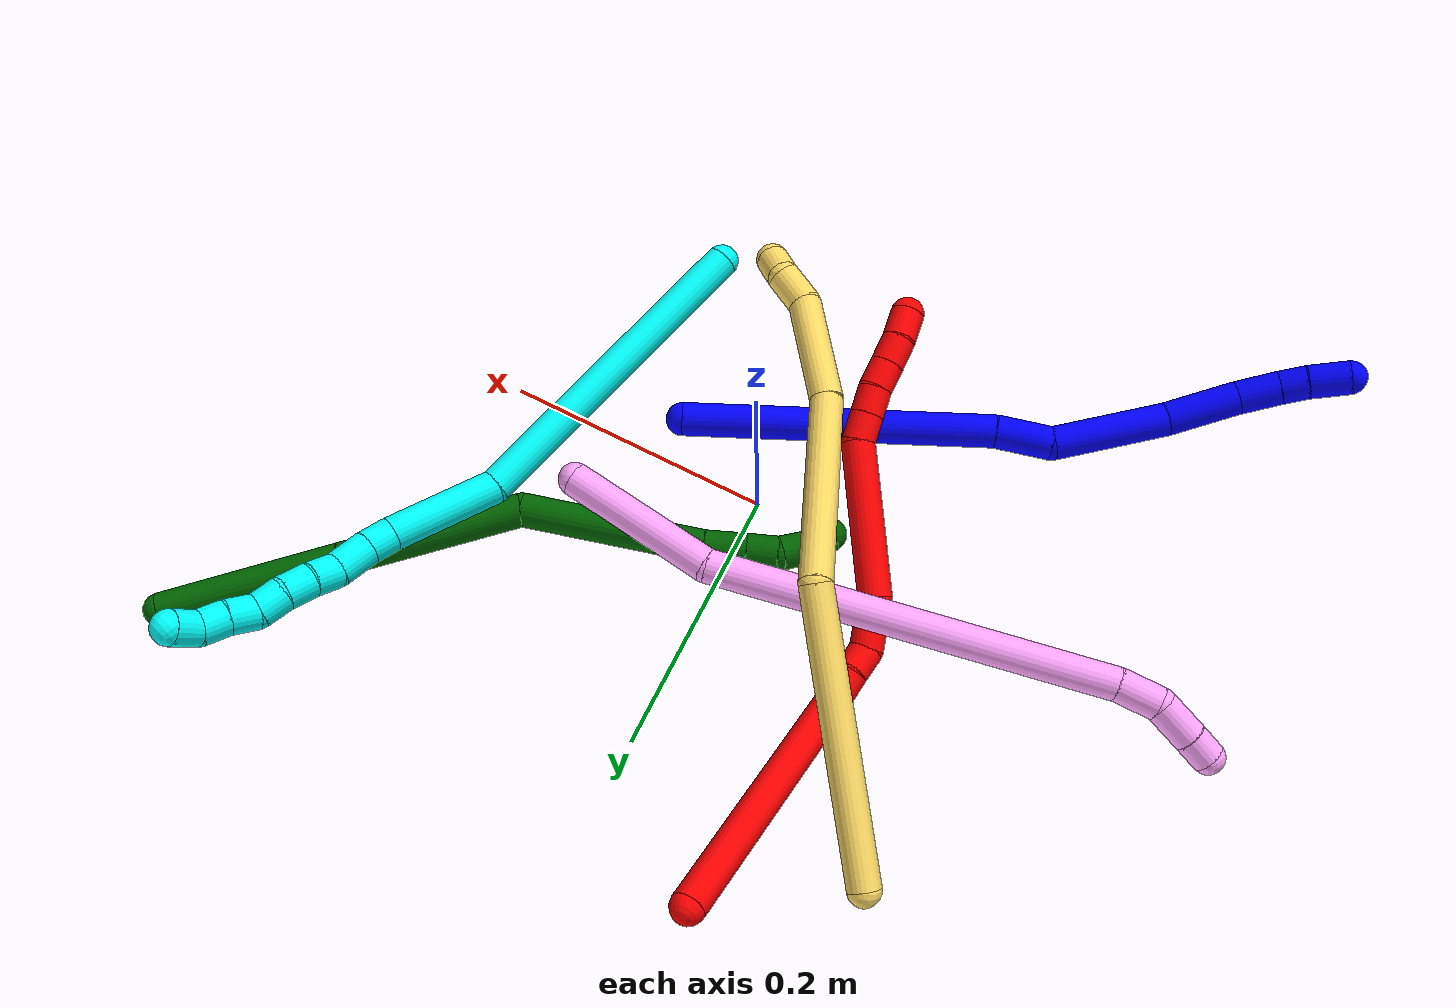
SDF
<sdf version="1.7">
 <world name="default">
  <plugin name="TubeGeneratorPlugin" filename="libtube_generator_plugin.so"/>
  <model name="photoneo_s_sensor">
   <static>1</static>
   <pose>0 0 2 1.57079 1.57079 3.14159</pose>
   <link name="link">
    <inertial><mass>0.1</mass></inertial>
    <sensor name="sensor" type="depth">
     <update_rate>30</update_rate>
     <camera>
      <horizontal_fov>1.22</horizontal_fov>
      <image><width>1920</width><height>1200</height><format>B8G8R8</format></image>
      <clip><near>0.1</near><far>4</far></clip>
      <depth_camera><output>points</output></depth_camera>
     </camera>
     <plugin name="camera_plugin" filename="libgazebo_ros_depth_camera.so">
      <baseline>0.2</baseline>
      <alwaysOn>1</alwaysOn>
      <updateRate>0.0</updateRate>
      <cameraName>camera_ir</cameraName>
      <imageTopicName>/camera/color/image_raw</imageTopicName>
      <cameraInfoTopicName>/camera/color/camera_info</cameraInfoTopicName>
      <depthImageTopicName>/camera/depth/image_raw</depthImageTopicName>
      <depthImageCameraInfoTopicName>/camera/depth/camera_info</depthImageCameraInfoTopicName>
      <pointCloudTopicName>/camera/depth/points</pointCloudTopicName>
      <frameName>fr_optical</frameName>
      <pointCloudCutoff>0.1</pointCloudCutoff>
      <pointCloudCutoffMax>2.0</pointCloudCutoffMax>
      <distortionK1>0</distortionK1>
      <distortionK2>0</distortionK2>
      <distortionK3>0</distortionK3>
      <distortionT1>0</distortionT1>
      <distortionT2>0</distortionT2>
      <CxPrime>0</CxPrime>
      <Cx>0</Cx>
      <Cy>0</Cy>
      <focalLength>0</focalLength>
      <hackBaseline>0</hackBaseline>
     </plugin>
    </sensor>
   </link>
  </model>
  <gravity>0 0 -9.8</gravity>
  <magnetic_field>6e-06 2.3e-05 -4.2e-05</magnetic_field>
  <atmosphere type="adiabatic"/>
  <physics name="default_physics" default="0" type="ode">
   <max_step_size>0.003</max_step_size>
   <real_time_factor>1</real_time_factor>
   <real_time_update_rate>1000</real_time_update_rate>
   <max_contacts>10000</max_contacts>
   <ode>
    <solver>
     <type>quick</type>
     <iters>100</iters>
     <sor>1.3</sor>
     <use_dynamic_moi_rescaling>0</use_dynamic_moi_rescaling>
    </solver>
    <constraints>
     <contact_max_correcting_vel>0</contact_max_correcting_vel>
     <contact_surface_layer>0.001</contact_surface_layer>
     <cfm>0</cfm>
     <erp>0.2</erp>
    </constraints>
   </ode>
  </physics>
  <scene><ambient>0.4 0.4 0.4 1</ambient><background>0.7 0.7 0.7 1</background><shadows>0</shadows></scene>
  <audio><device>default</device></audio>
  <spherical_coordinates>
   <surface_model>EARTH_WGS84</surface_model>
   <latitude_deg>0</latitude_deg>
   <longitude_deg>0</longitude_deg>
   <elevation>0</elevation>
   <heading_deg>0</heading_deg>
  </spherical_coordinates>
  <model name="bin">
   <static>1</static>
   <link name="bottom">
    <collision name="collision-bottom">
     <pose>0 0 -0.01 0 -0 0</pose>
     <geometry><box><size>0.8 0.6 0.02</size></box></geometry>
     <surface>
      <friction><ode><mu>100</mu><mu2>100</mu2></ode></friction>
      <contact><collide_bitmask>65535</collide_bitmask></contact>
     </surface>
    </collision>
   </link>
   <link name="west_wall">
    <collision name="collision-west_wall">
     <pose>-0.41 0 0.1 0 -0 0</pose>
     <geometry><box><size>0.02 0.6 0.2</size></box></geometry>
     <surface>
      <friction><ode><mu>100</mu><mu2>100</mu2></ode></friction>
      <contact><collide_bitmask>65535</collide_bitmask></contact>
     </surface>
    </collision>
   </link>
   <link name="east_wall">
    <collision name="collision-east_wall">
     <pose>0.41 0 0.1 0 -0 0</pose>
     <geometry><box><size>0.02 0.6 0.2</size></box></geometry>
     <surface>
      <friction><ode><mu>100</mu><mu2>100</mu2></ode></friction>
      <contact><collide_bitmask>65535</collide_bitmask></contact>
     </surface>
    </collision>
   </link>
   <link name="south_wall">
    <collision name="collision-south_wall">
     <pose>0 -0.31 0.1 0 -0 0</pose>
     <geometry><box><size>0.8 0.02 0.2</size></box></geometry>
     <surface>
      <friction><ode><mu>100</mu><mu2>100</mu2></ode></friction>
      <contact><collide_bitmask>65535</collide_bitmask></contact>
     </surface>
    </collision>
   </link>
   <link name="north_wall">
    <collision name="collision-north_wall">
     <pose>0 0.31 0.1 0 -0 0</pose>
     <geometry><box><size>0.8 0.02 0.2</size></box></geometry>
     <surface>
      <friction><ode><mu>100</mu><mu2>100</mu2></ode></friction>
      <contact><collide_bitmask>65535</collide_bitmask></contact>
     </surface>
    </collision>
   </link>
  </model>
  <model name="1">
   <static>0</static>
   <link name="1">
    <collision name="collision-cylinder-e_1_1_4">
     <pose>-0.082228 -0.037469 0.073331 0.472373 -0.784665 -0.198524</pose>
     <geometry><cylinder><radius>0.0125</radius><length>0.232747</length></cylinder></geometry>
     <surface>
      <friction><ode><mu>1.16</mu><mu2>1.16</mu2><slip1>0</slip1><slip2>0</slip2></ode></friction>
      <contact><ode><kp>1e+06</kp><kd>1</kd><max_vel>0</max_vel><min_depth>0.001</min_depth></ode></contact>
     </surface>
    </collision>
    <visual name="visual-cylinder-e_1_1_4">
     <pose>-0.082228 -0.037469 0.073331 0.472373 -0.784665 -0.198524</pose>
     <geometry><cylinder><radius>0.0125</radius><length>0.232747</length></cylinder></geometry>
     <material><ambient>0 0 1 1</ambient></material>
    </visual>
    <collision name="collision-cylinder-e_2_4_5">
     <pose>-0.179664 -0.084913 0.157886 0.72654 -0.791733 -0.31511</pose>
     <geometry><cylinder><radius>0.0125</radius><length>0.042745</length></cylinder></geometry>
     <surface>
      <friction><ode><mu>1.16</mu><mu2>1.16</mu2><slip1>0</slip1><slip2>0</slip2></ode></friction>
      <contact><ode><kp>1e+06</kp><kd>1</kd><max_vel>0</max_vel><min_depth>0.001</min_depth></ode></contact>
     </surface>
    </collision>
    <visual name="visual-cylinder-e_2_4_5">
     <pose>-0.179664 -0.084913 0.157886 0.72654 -0.791733 -0.31511</pose>
     <geometry><cylinder><radius>0.0125</radius><length>0.042745</length></cylinder></geometry>
     <material><ambient>0 0 1 1</ambient></material>
    </visual>
    <collision name="collision-cylinder-e_3_5_6">
     <pose>-0.222236 -0.09992 0.20323 0.146435 -0.670713 -0.051116</pose>
     <geometry><cylinder><radius>0.0125</radius><length>0.088051</length></cylinder></geometry>
     <surface>
      <friction><ode><mu>1.16</mu><mu2>1.16</mu2><slip1>0</slip1><slip2>0</slip2></ode></friction>
      <contact><ode><kp>1e+06</kp><kd>1</kd><max_vel>0</max_vel><min_depth>0.001</min_depth></ode></contact>
     </surface>
    </collision>
    <visual name="visual-cylinder-e_3_5_6">
     <pose>-0.222236 -0.09992 0.20323 0.146435 -0.670713 -0.051116</pose>
     <geometry><cylinder><radius>0.0125</radius><length>0.088051</length></cylinder></geometry>
     <material><ambient>0 0 1 1</ambient></material>
    </visual>
    <collision name="collision-cylinder-e_4_6_7">
     <pose>-0.26871 -0.105038 0.257065 0.004344 -0.769812 -0.00176</pose>
     <geometry><cylinder><radius>0.0125</radius><length>0.054914</length></cylinder></geometry>
     <surface>
      <friction><ode><mu>1.16</mu><mu2>1.16</mu2><slip1>0</slip1><slip2>0</slip2></ode></friction>
      <contact><ode><kp>1e+06</kp><kd>1</kd><max_vel>0</max_vel><min_depth>0.001</min_depth></ode></contact>
     </surface>
    </collision>
    <visual name="visual-cylinder-e_4_6_7">
     <pose>-0.26871 -0.105038 0.257065 0.004344 -0.769812 -0.00176</pose>
     <geometry><cylinder><radius>0.0125</radius><length>0.054914</length></cylinder></geometry>
     <material><ambient>0 0 1 1</ambient></material>
    </visual>
    <collision name="collision-cylinder-e_5_7_8">
     <pose>-0.300153 -0.105564 0.286708 0.044278 -0.892513 -0.021188</pose>
     <geometry><cylinder><radius>0.0125</radius><length>0.031678</length></cylinder></geometry>
     <surface>
      <friction><ode><mu>1.16</mu><mu2>1.16</mu2><slip1>0</slip1><slip2>0</slip2></ode></friction>
      <contact><ode><kp>1e+06</kp><kd>1</kd><max_vel>0</max_vel><min_depth>0.001</min_depth></ode></contact>
     </surface>
    </collision>
    <visual name="visual-cylinder-e_5_7_8">
     <pose>-0.300153 -0.105564 0.286708 0.044278 -0.892513 -0.021188</pose>
     <geometry><cylinder><radius>0.0125</radius><length>0.031678</length></cylinder></geometry>
     <material><ambient>0 0 1 1</ambient></material>
    </visual>
    <collision name="collision-cylinder-e_6_8_9">
     <pose>-0.320886 -0.106366 0.302085 0.066419 -0.994394 -0.036053</pose>
     <geometry><cylinder><radius>0.0125</radius><length>0.020036</length></cylinder></geometry>
     <surface>
      <friction><ode><mu>1.16</mu><mu2>1.16</mu2><slip1>0</slip1><slip2>0</slip2></ode></friction>
      <contact><ode><kp>1e+06</kp><kd>1</kd><max_vel>0</max_vel><min_depth>0.001</min_depth></ode></contact>
     </surface>
    </collision>
    <visual name="visual-cylinder-e_6_8_9">
     <pose>-0.320886 -0.106366 0.302085 0.066419 -0.994394 -0.036053</pose>
     <geometry><cylinder><radius>0.0125</radius><length>0.020036</length></cylinder></geometry>
     <material><ambient>0 0 1 1</ambient></material>
    </visual>
    <collision name="collision-cylinder-e_7_9_2">
     <pose>-0.341603 -0.108738 0.315698 0.241291 -0.971853 -0.127889</pose>
     <geometry><cylinder><radius>0.0125</radius><length>0.02983</length></cylinder></geometry>
     <surface>
      <friction><ode><mu>1.16</mu><mu2>1.16</mu2><slip1>0</slip1><slip2>0</slip2></ode></friction>
      <contact><ode><kp>1e+06</kp><kd>1</kd><max_vel>0</max_vel><min_depth>0.001</min_depth></ode></contact>
     </surface>
    </collision>
    <visual name="visual-cylinder-e_7_9_2">
     <pose>-0.341603 -0.108738 0.315698 0.241291 -0.971853 -0.127889</pose>
     <geometry><cylinder><radius>0.0125</radius><length>0.02983</length></cylinder></geometry>
     <material><ambient>0 0 1 1</ambient></material>
    </visual>
    <collision name="collision-sphere-2">
     <pose>-0.353922 -0.110747 0.323862 0 -0 0</pose>
     <geometry><sphere><radius>0.0125</radius></sphere></geometry>
     <surface>
      <friction><ode><mu>1.16</mu><mu2>1.16</mu2><slip1>0</slip1><slip2>0</slip2></ode></friction>
      <contact><ode><kp>1e+06</kp><kd>1</kd><max_vel>0</max_vel><min_depth>0.001</min_depth></ode></contact>
     </surface>
    </collision>
    <visual name="visual-sphere-2">
     <pose>-0.353922 -0.110747 0.323862 0 -0 0</pose>
     <geometry><sphere><radius>0.0125</radius></sphere></geometry>
     <material><ambient>0 0 1 1</ambient></material>
    </visual>
    <collision name="collision-sphere-9">
     <pose>-0.329285 -0.106728 0.307533 0 -0 0</pose>
     <geometry><sphere><radius>0.0125</radius></sphere></geometry>
     <surface>
      <friction><ode><mu>1.16</mu><mu2>1.16</mu2><slip1>0</slip1><slip2>0</slip2></ode></friction>
      <contact><ode><kp>1e+06</kp><kd>1</kd><max_vel>0</max_vel><min_depth>0.001</min_depth></ode></contact>
     </surface>
    </collision>
    <visual name="visual-sphere-9">
     <pose>-0.329285 -0.106728 0.307533 0 -0 0</pose>
     <geometry><sphere><radius>0.0125</radius></sphere></geometry>
     <material><ambient>0 0 1 1</ambient></material>
    </visual>
    <collision name="collision-sphere-4">
     <pose>-0.164456 -0.074938 0.146662 0 -0 0</pose>
     <geometry><sphere><radius>0.0125</radius></sphere></geometry>
     <surface>
      <friction><ode><mu>1.16</mu><mu2>1.16</mu2><slip1>0</slip1><slip2>0</slip2></ode></friction>
      <contact><ode><kp>1e+06</kp><kd>1</kd><max_vel>0</max_vel><min_depth>0.001</min_depth></ode></contact>
     </surface>
    </collision>
    <visual name="visual-sphere-4">
     <pose>-0.164456 -0.074938 0.146662 0 -0 0</pose>
     <geometry><sphere><radius>0.0125</radius></sphere></geometry>
     <material><ambient>0 0 1 1</ambient></material>
    </visual>
    <collision name="collision-sphere-1">
     <geometry><sphere><radius>0.0125</radius></sphere></geometry>
     <surface>
      <friction><ode><mu>1.16</mu><mu2>1.16</mu2><slip1>0</slip1><slip2>0</slip2></ode></friction>
      <contact><ode><kp>1e+06</kp><kd>1</kd><max_vel>0</max_vel><min_depth>0.001</min_depth></ode></contact>
     </surface>
    </collision>
    <visual name="visual-sphere-1">
     <geometry><sphere><radius>0.0125</radius></sphere></geometry>
     <material><ambient>0 0 1 1</ambient></material>
    </visual>
    <collision name="collision-sphere-8">
     <pose>-0.312486 -0.106004 0.296637 0 -0 0</pose>
     <geometry><sphere><radius>0.0125</radius></sphere></geometry>
     <surface>
      <friction><ode><mu>1.16</mu><mu2>1.16</mu2><slip1>0</slip1><slip2>0</slip2></ode></friction>
      <contact><ode><kp>1e+06</kp><kd>1</kd><max_vel>0</max_vel><min_depth>0.001</min_depth></ode></contact>
     </surface>
    </collision>
    <visual name="visual-sphere-8">
     <pose>-0.312486 -0.106004 0.296637 0 -0 0</pose>
     <geometry><sphere><radius>0.0125</radius></sphere></geometry>
     <material><ambient>0 0 1 1</ambient></material>
    </visual>
    <collision name="collision-sphere-5">
     <pose>-0.194872 -0.094888 0.169111 0 -0 0</pose>
     <geometry><sphere><radius>0.0125</radius></sphere></geometry>
     <surface>
      <friction><ode><mu>1.16</mu><mu2>1.16</mu2><slip1>0</slip1><slip2>0</slip2></ode></friction>
      <contact><ode><kp>1e+06</kp><kd>1</kd><max_vel>0</max_vel><min_depth>0.001</min_depth></ode></contact>
     </surface>
    </collision>
    <visual name="visual-sphere-5">
     <pose>-0.194872 -0.094888 0.169111 0 -0 0</pose>
     <geometry><sphere><radius>0.0125</radius></sphere></geometry>
     <material><ambient>0 0 1 1</ambient></material>
    </visual>
    <collision name="collision-sphere-6">
     <pose>-0.2496 -0.104953 0.23735 0 -0 0</pose>
     <geometry><sphere><radius>0.0125</radius></sphere></geometry>
     <surface>
      <friction><ode><mu>1.16</mu><mu2>1.16</mu2><slip1>0</slip1><slip2>0</slip2></ode></friction>
      <contact><ode><kp>1e+06</kp><kd>1</kd><max_vel>0</max_vel><min_depth>0.001</min_depth></ode></contact>
     </surface>
    </collision>
    <visual name="visual-sphere-6">
     <pose>-0.2496 -0.104953 0.23735 0 -0 0</pose>
     <geometry><sphere><radius>0.0125</radius></sphere></geometry>
     <material><ambient>0 0 1 1</ambient></material>
    </visual>
    <collision name="collision-sphere-7">
     <pose>-0.28782 -0.105124 0.27678 0 -0 0</pose>
     <geometry><sphere><radius>0.0125</radius></sphere></geometry>
     <surface>
      <friction><ode><mu>1.16</mu><mu2>1.16</mu2><slip1>0</slip1><slip2>0</slip2></ode></friction>
      <contact><ode><kp>1e+06</kp><kd>1</kd><max_vel>0</max_vel><min_depth>0.001</min_depth></ode></contact>
     </surface>
    </collision>
    <visual name="visual-sphere-7">
     <pose>-0.28782 -0.105124 0.27678 0 -0 0</pose>
     <geometry><sphere><radius>0.0125</radius></sphere></geometry>
     <material><ambient>0 0 1 1</ambient></material>
    </visual>
    <inertial>
     <pose>-0.174539 -0.07127 0.160759 0 -0 0</pose>
     <mass>0.5</mass>
     <inertia>
      <ixx>0.000624</ixx>
      <ixy>0</ixy>
      <ixz>0</ixz>
      <iyy>0.000923</iyy>
      <iyz>0</iyz>
      <izz>0.001188</izz>
     </inertia>
    </inertial>
   </link>
   <pose>0.078316 -0.031226 0.012327 2.28516 0.752922 0.153311</pose>
  </model>
  <model name="2">
   <static>0</static>
   <link name="2">
    <collision name="collision-cylinder-e_1_1_4">
     <pose>-0.009499 -0.002422 -0.095594 3.11626 -0.099008 -2.64094</pose>
     <geometry><cylinder><radius>0.0125</radius><length>0.19219</length></cylinder></geometry>
     <surface>
      <friction><ode><mu>1.16</mu><mu2>1.16</mu2><slip1>0</slip1><slip2>0</slip2></ode></friction>
      <contact><ode><kp>1e+06</kp><kd>1</kd><max_vel>0</max_vel><min_depth>0.001</min_depth></ode></contact>
     </surface>
    </collision>
    <visual name="visual-cylinder-e_1_1_4">
     <pose>-0.009499 -0.002422 -0.095594 3.11626 -0.099008 -2.64094</pose>
     <geometry><cylinder><radius>0.0125</radius><length>0.19219</length></cylinder></geometry>
     <material><ambient>1 0 0 1</ambient></material>
    </visual>
    <collision name="collision-cylinder-e_2_4_5">
     <pose>-0.021344 -0.011562 -0.203692 2.64867 -0.16385 -0.630951</pose>
     <geometry><cylinder><radius>0.0125</radius><length>0.028776</length></cylinder></geometry>
     <surface>
      <friction><ode><mu>1.16</mu><mu2>1.16</mu2><slip1>0</slip1><slip2>0</slip2></ode></friction>
      <contact><ode><kp>1e+06</kp><kd>1</kd><max_vel>0</max_vel><min_depth>0.001</min_depth></ode></contact>
     </surface>
    </collision>
    <visual name="visual-cylinder-e_2_4_5">
     <pose>-0.021344 -0.011562 -0.203692 2.64867 -0.16385 -0.630951</pose>
     <geometry><cylinder><radius>0.0125</radius><length>0.028776</length></cylinder></geometry>
     <material><ambient>1 0 0 1</ambient></material>
    </visual>
    <collision name="collision-cylinder-e_3_5_6">
     <pose>-0.025397 -0.021616 -0.225569 2.79949 -0.169842 -0.915746</pose>
     <geometry><cylinder><radius>0.0125</radius><length>0.020187</length></cylinder></geometry>
     <surface>
      <friction><ode><mu>1.16</mu><mu2>1.16</mu2><slip1>0</slip1><slip2>0</slip2></ode></friction>
      <contact><ode><kp>1e+06</kp><kd>1</kd><max_vel>0</max_vel><min_depth>0.001</min_depth></ode></contact>
     </surface>
    </collision>
    <visual name="visual-cylinder-e_3_5_6">
     <pose>-0.025397 -0.021616 -0.225569 2.79949 -0.169842 -0.915746</pose>
     <geometry><cylinder><radius>0.0125</radius><length>0.020187</length></cylinder></geometry>
     <material><ambient>1 0 0 1</ambient></material>
    </visual>
    <collision name="collision-cylinder-e_4_6_7">
     <pose>-0.023405 -0.03679 -0.248853 2.43663 0.19977 0.531987</pose>
     <geometry><cylinder><radius>0.0125</radius><length>0.037274</length></cylinder></geometry>
     <surface>
      <friction><ode><mu>1.16</mu><mu2>1.16</mu2><slip1>0</slip1><slip2>0</slip2></ode></friction>
      <contact><ode><kp>1e+06</kp><kd>1</kd><max_vel>0</max_vel><min_depth>0.001</min_depth></ode></contact>
     </surface>
    </collision>
    <visual name="visual-cylinder-e_4_6_7">
     <pose>-0.023405 -0.03679 -0.248853 2.43663 0.19977 0.531987</pose>
     <geometry><cylinder><radius>0.0125</radius><length>0.037274</length></cylinder></geometry>
     <material><ambient>1 0 0 1</ambient></material>
    </visual>
    <collision name="collision-cylinder-e_5_7_8">
     <pose>0.007134 -0.081395 -0.302058 2.44649 0.483146 1.19454</pose>
     <geometry><cylinder><radius>0.0125</radius><length>0.115553</length></cylinder></geometry>
     <surface>
      <friction><ode><mu>1.16</mu><mu2>1.16</mu2><slip1>0</slip1><slip2>0</slip2></ode></friction>
      <contact><ode><kp>1e+06</kp><kd>1</kd><max_vel>0</max_vel><min_depth>0.001</min_depth></ode></contact>
     </surface>
    </collision>
    <visual name="visual-cylinder-e_5_7_8">
     <pose>0.007134 -0.081395 -0.302058 2.44649 0.483146 1.19454</pose>
     <geometry><cylinder><radius>0.0125</radius><length>0.115553</length></cylinder></geometry>
     <material><ambient>1 0 0 1</ambient></material>
    </visual>
    <collision name="collision-cylinder-e_6_8_9">
     <pose>0.034811 -0.120569 -0.349664 2.48506 0.079397 0.232191</pose>
     <geometry><cylinder><radius>0.0125</radius><length>0.021057</length></cylinder></geometry>
     <surface>
      <friction><ode><mu>1.16</mu><mu2>1.16</mu2><slip1>0</slip1><slip2>0</slip2></ode></friction>
      <contact><ode><kp>1e+06</kp><kd>1</kd><max_vel>0</max_vel><min_depth>0.001</min_depth></ode></contact>
     </surface>
    </collision>
    <visual name="visual-cylinder-e_6_8_9">
     <pose>0.034811 -0.120569 -0.349664 2.48506 0.079397 0.232191</pose>
     <geometry><cylinder><radius>0.0125</radius><length>0.021057</length></cylinder></geometry>
     <material><ambient>1 0 0 1</ambient></material>
    </visual>
    <collision name="collision-cylinder-e_7_9_10">
     <pose>0.036464 -0.133253 -0.366084 2.48267 0.079613 0.231917</pose>
     <geometry><cylinder><radius>0.0125</radius><length>0.020572</length></cylinder></geometry>
     <surface>
      <friction><ode><mu>1.16</mu><mu2>1.16</mu2><slip1>0</slip1><slip2>0</slip2></ode></friction>
      <contact><ode><kp>1e+06</kp><kd>1</kd><max_vel>0</max_vel><min_depth>0.001</min_depth></ode></contact>
     </surface>
    </collision>
    <visual name="visual-cylinder-e_7_9_10">
     <pose>0.036464 -0.133253 -0.366084 2.48267 0.079613 0.231917</pose>
     <geometry><cylinder><radius>0.0125</radius><length>0.020572</length></cylinder></geometry>
     <material><ambient>1 0 0 1</ambient></material>
    </visual>
    <collision name="collision-cylinder-e_8_10_11">
     <pose>0.036832 -0.144894 -0.382982 2.5938 -0.043641 -0.155042</pose>
     <geometry><cylinder><radius>0.0125</radius><length>0.020615</length></cylinder></geometry>
     <surface>
      <friction><ode><mu>1.16</mu><mu2>1.16</mu2><slip1>0</slip1><slip2>0</slip2></ode></friction>
      <contact><ode><kp>1e+06</kp><kd>1</kd><max_vel>0</max_vel><min_depth>0.001</min_depth></ode></contact>
     </surface>
    </collision>
    <visual name="visual-cylinder-e_8_10_11">
     <pose>0.036832 -0.144894 -0.382982 2.5938 -0.043641 -0.155042</pose>
     <geometry><cylinder><radius>0.0125</radius><length>0.020615</length></cylinder></geometry>
     <material><ambient>1 0 0 1</ambient></material>
    </visual>
    <collision name="collision-cylinder-e_9_11_12">
     <pose>0.035981 -0.155892 -0.400851 2.58606 -0.03751 -0.131375</pose>
     <geometry><cylinder><radius>0.0125</radius><length>0.021386</length></cylinder></geometry>
     <surface>
      <friction><ode><mu>1.16</mu><mu2>1.16</mu2><slip1>0</slip1><slip2>0</slip2></ode></friction>
      <contact><ode><kp>1e+06</kp><kd>1</kd><max_vel>0</max_vel><min_depth>0.001</min_depth></ode></contact>
     </surface>
    </collision>
    <visual name="visual-cylinder-e_9_11_12">
     <pose>0.035981 -0.155892 -0.400851 2.58606 -0.03751 -0.131375</pose>
     <geometry><cylinder><radius>0.0125</radius><length>0.021386</length></cylinder></geometry>
     <material><ambient>1 0 0 1</ambient></material>
    </visual>
    <collision name="collision-cylinder-e_10_12_2">
     <pose>0.036667 -0.166573 -0.419865 2.67174 0.097264 0.401224</pose>
     <geometry><cylinder><radius>0.0125</radius><length>0.022392</length></cylinder></geometry>
     <surface>
      <friction><ode><mu>1.16</mu><mu2>1.16</mu2><slip1>0</slip1><slip2>0</slip2></ode></friction>
      <contact><ode><kp>1e+06</kp><kd>1</kd><max_vel>0</max_vel><min_depth>0.001</min_depth></ode></contact>
     </surface>
    </collision>
    <visual name="visual-cylinder-e_10_12_2">
     <pose>0.036667 -0.166573 -0.419865 2.67174 0.097264 0.401224</pose>
     <geometry><cylinder><radius>0.0125</radius><length>0.022392</length></cylinder></geometry>
     <material><ambient>1 0 0 1</ambient></material>
    </visual>
    <collision name="collision-sphere-2">
     <pose>0.037755 -0.171618 -0.429801 0 -0 0</pose>
     <geometry><sphere><radius>0.0125</radius></sphere></geometry>
     <surface>
      <friction><ode><mu>1.16</mu><mu2>1.16</mu2><slip1>0</slip1><slip2>0</slip2></ode></friction>
      <contact><ode><kp>1e+06</kp><kd>1</kd><max_vel>0</max_vel><min_depth>0.001</min_depth></ode></contact>
     </surface>
    </collision>
    <visual name="visual-sphere-2">
     <pose>0.037755 -0.171618 -0.429801 0 -0 0</pose>
     <geometry><sphere><radius>0.0125</radius></sphere></geometry>
     <material><ambient>1 0 0 1</ambient></material>
    </visual>
    <collision name="collision-sphere-12">
     <pose>0.03558 -0.161528 -0.40993 0 -0 0</pose>
     <geometry><sphere><radius>0.0125</radius></sphere></geometry>
     <surface>
      <friction><ode><mu>1.16</mu><mu2>1.16</mu2><slip1>0</slip1><slip2>0</slip2></ode></friction>
      <contact><ode><kp>1e+06</kp><kd>1</kd><max_vel>0</max_vel><min_depth>0.001</min_depth></ode></contact>
     </surface>
    </collision>
    <visual name="visual-sphere-12">
     <pose>0.03558 -0.161528 -0.40993 0 -0 0</pose>
     <geometry><sphere><radius>0.0125</radius></sphere></geometry>
     <material><ambient>1 0 0 1</ambient></material>
    </visual>
    <collision name="collision-sphere-11">
     <pose>0.036382 -0.150257 -0.391772 0 -0 0</pose>
     <geometry><sphere><radius>0.0125</radius></sphere></geometry>
     <surface>
      <friction><ode><mu>1.16</mu><mu2>1.16</mu2><slip1>0</slip1><slip2>0</slip2></ode></friction>
      <contact><ode><kp>1e+06</kp><kd>1</kd><max_vel>0</max_vel><min_depth>0.001</min_depth></ode></contact>
     </surface>
    </collision>
    <visual name="visual-sphere-11">
     <pose>0.036382 -0.150257 -0.391772 0 -0 0</pose>
     <geometry><sphere><radius>0.0125</radius></sphere></geometry>
     <material><ambient>1 0 0 1</ambient></material>
    </visual>
    <collision name="collision-sphere-10">
     <pose>0.037282 -0.139531 -0.374191 0 -0 0</pose>
     <geometry><sphere><radius>0.0125</radius></sphere></geometry>
     <surface>
      <friction><ode><mu>1.16</mu><mu2>1.16</mu2><slip1>0</slip1><slip2>0</slip2></ode></friction>
      <contact><ode><kp>1e+06</kp><kd>1</kd><max_vel>0</max_vel><min_depth>0.001</min_depth></ode></contact>
     </surface>
    </collision>
    <visual name="visual-sphere-10">
     <pose>0.037282 -0.139531 -0.374191 0 -0 0</pose>
     <geometry><sphere><radius>0.0125</radius></sphere></geometry>
     <material><ambient>1 0 0 1</ambient></material>
    </visual>
    <collision name="collision-sphere-9">
     <pose>0.035646 -0.126975 -0.357977 0 -0 0</pose>
     <geometry><sphere><radius>0.0125</radius></sphere></geometry>
     <surface>
      <friction><ode><mu>1.16</mu><mu2>1.16</mu2><slip1>0</slip1><slip2>0</slip2></ode></friction>
      <contact><ode><kp>1e+06</kp><kd>1</kd><max_vel>0</max_vel><min_depth>0.001</min_depth></ode></contact>
     </surface>
    </collision>
    <visual name="visual-sphere-9">
     <pose>0.035646 -0.126975 -0.357977 0 -0 0</pose>
     <geometry><sphere><radius>0.0125</radius></sphere></geometry>
     <material><ambient>1 0 0 1</ambient></material>
    </visual>
    <collision name="collision-sphere-4">
     <pose>-0.018997 -0.004845 -0.191187 0 -0 0</pose>
     <geometry><sphere><radius>0.0125</radius></sphere></geometry>
     <surface>
      <friction><ode><mu>1.16</mu><mu2>1.16</mu2><slip1>0</slip1><slip2>0</slip2></ode></friction>
      <contact><ode><kp>1e+06</kp><kd>1</kd><max_vel>0</max_vel><min_depth>0.001</min_depth></ode></contact>
     </surface>
    </collision>
    <visual name="visual-sphere-4">
     <pose>-0.018997 -0.004845 -0.191187 0 -0 0</pose>
     <geometry><sphere><radius>0.0125</radius></sphere></geometry>
     <material><ambient>1 0 0 1</ambient></material>
    </visual>
    <collision name="collision-sphere-1">
     <geometry><sphere><radius>0.0125</radius></sphere></geometry>
     <surface>
      <friction><ode><mu>1.16</mu><mu2>1.16</mu2><slip1>0</slip1><slip2>0</slip2></ode></friction>
      <contact><ode><kp>1e+06</kp><kd>1</kd><max_vel>0</max_vel><min_depth>0.001</min_depth></ode></contact>
     </surface>
    </collision>
    <visual name="visual-sphere-1">
     <geometry><sphere><radius>0.0125</radius></sphere></geometry>
     <material><ambient>1 0 0 1</ambient></material>
    </visual>
    <collision name="collision-sphere-8">
     <pose>0.033975 -0.114163 -0.341351 0 -0 0</pose>
     <geometry><sphere><radius>0.0125</radius></sphere></geometry>
     <surface>
      <friction><ode><mu>1.16</mu><mu2>1.16</mu2><slip1>0</slip1><slip2>0</slip2></ode></friction>
      <contact><ode><kp>1e+06</kp><kd>1</kd><max_vel>0</max_vel><min_depth>0.001</min_depth></ode></contact>
     </surface>
    </collision>
    <visual name="visual-sphere-8">
     <pose>0.033975 -0.114163 -0.341351 0 -0 0</pose>
     <geometry><sphere><radius>0.0125</radius></sphere></geometry>
     <material><ambient>1 0 0 1</ambient></material>
    </visual>
    <collision name="collision-sphere-5">
     <pose>-0.023691 -0.018279 -0.216198 0 -0 0</pose>
     <geometry><sphere><radius>0.0125</radius></sphere></geometry>
     <surface>
      <friction><ode><mu>1.16</mu><mu2>1.16</mu2><slip1>0</slip1><slip2>0</slip2></ode></friction>
      <contact><ode><kp>1e+06</kp><kd>1</kd><max_vel>0</max_vel><min_depth>0.001</min_depth></ode></contact>
     </surface>
    </collision>
    <visual name="visual-sphere-5">
     <pose>-0.023691 -0.018279 -0.216198 0 -0 0</pose>
     <geometry><sphere><radius>0.0125</radius></sphere></geometry>
     <material><ambient>1 0 0 1</ambient></material>
    </visual>
    <collision name="collision-sphere-6">
     <pose>-0.027103 -0.024954 -0.234941 0 -0 0</pose>
     <geometry><sphere><radius>0.0125</radius></sphere></geometry>
     <surface>
      <friction><ode><mu>1.16</mu><mu2>1.16</mu2><slip1>0</slip1><slip2>0</slip2></ode></friction>
      <contact><ode><kp>1e+06</kp><kd>1</kd><max_vel>0</max_vel><min_depth>0.001</min_depth></ode></contact>
     </surface>
    </collision>
    <visual name="visual-sphere-6">
     <pose>-0.027103 -0.024954 -0.234941 0 -0 0</pose>
     <geometry><sphere><radius>0.0125</radius></sphere></geometry>
     <material><ambient>1 0 0 1</ambient></material>
    </visual>
    <collision name="collision-sphere-7">
     <pose>-0.019707 -0.048627 -0.262765 0 -0 0</pose>
     <geometry><sphere><radius>0.0125</radius></sphere></geometry>
     <surface>
      <friction><ode><mu>1.16</mu><mu2>1.16</mu2><slip1>0</slip1><slip2>0</slip2></ode></friction>
      <contact><ode><kp>1e+06</kp><kd>1</kd><max_vel>0</max_vel><min_depth>0.001</min_depth></ode></contact>
     </surface>
    </collision>
    <visual name="visual-sphere-7">
     <pose>-0.019707 -0.048627 -0.262765 0 -0 0</pose>
     <geometry><sphere><radius>0.0125</radius></sphere></geometry>
     <material><ambient>1 0 0 1</ambient></material>
    </visual>
    <inertial>
     <pose>0.001665 -0.054684 -0.227459 0 -0 0</pose>
     <mass>0.5</mass>
     <inertia>
      <ixx>-0.000636</ixx>
      <ixy>0</ixy>
      <ixz>0</ixz>
      <iyy>0.000324</iyy>
      <iyz>0</iyz>
      <izz>6.4e-05</izz>
     </inertia>
    </inertial>
   </link>
   <pose>-0.096047 0.288186 0.095536 -1.08545 0.109441 0.055014</pose>
  </model>
  <model name="3">
   <static>0</static>
   <link name="3">
    <collision name="collision-cylinder-e_1_1_4">
     <pose>0.001699 0.014832 0.123157 -0.119851 0.013694 -0.000822</pose>
     <geometry><cylinder><radius>0.0125</radius><length>0.248117</length></cylinder></geometry>
     <surface>
      <friction><ode><mu>1.16</mu><mu2>1.16</mu2><slip1>0</slip1><slip2>0</slip2></ode></friction>
      <contact><ode><kp>1e+06</kp><kd>1</kd><max_vel>0</max_vel><min_depth>0.001</min_depth></ode></contact>
     </surface>
    </collision>
    <visual name="visual-cylinder-e_1_1_4">
     <pose>0.001699 0.014832 0.123157 -0.119851 0.013694 -0.000822</pose>
     <geometry><cylinder><radius>0.0125</radius><length>0.248117</length></cylinder></geometry>
     <material><ambient>0.003922 1 0.996078 1</ambient></material>
    </visual>
    <collision name="collision-cylinder-e_2_4_5">
     <pose>0.009093 0.021577 0.286051 0.200741 0.139539 0.014075</pose>
     <geometry><cylinder><radius>0.0125</radius><length>0.0819</length></cylinder></geometry>
     <surface>
      <friction><ode><mu>1.16</mu><mu2>1.16</mu2><slip1>0</slip1><slip2>0</slip2></ode></friction>
      <contact><ode><kp>1e+06</kp><kd>1</kd><max_vel>0</max_vel><min_depth>0.001</min_depth></ode></contact>
     </surface>
    </collision>
    <visual name="visual-cylinder-e_2_4_5">
     <pose>0.009093 0.021577 0.286051 0.200741 0.139539 0.014075</pose>
     <geometry><cylinder><radius>0.0125</radius><length>0.0819</length></cylinder></geometry>
     <material><ambient>0.003922 1 0.996078 1</ambient></material>
    </visual>
    <collision name="collision-cylinder-e_3_5_6">
     <pose>0.014687 0.011601 0.335737 0.187747 -0.010026 -0.000944</pose>
     <geometry><cylinder><radius>0.0125</radius><length>0.020253</length></cylinder></geometry>
     <surface>
      <friction><ode><mu>1.16</mu><mu2>1.16</mu2><slip1>0</slip1><slip2>0</slip2></ode></friction>
      <contact><ode><kp>1e+06</kp><kd>1</kd><max_vel>0</max_vel><min_depth>0.001</min_depth></ode></contact>
     </surface>
    </collision>
    <visual name="visual-cylinder-e_3_5_6">
     <pose>0.014687 0.011601 0.335737 0.187747 -0.010026 -0.000944</pose>
     <geometry><cylinder><radius>0.0125</radius><length>0.020253</length></cylinder></geometry>
     <material><ambient>0.003922 1 0.996078 1</ambient></material>
    </visual>
    <collision name="collision-cylinder-e_4_6_7">
     <pose>0.01268 0.007829 0.359215 0.138232 -0.138585 -0.009609</pose>
     <geometry><cylinder><radius>0.0125</radius><length>0.027586</length></cylinder></geometry>
     <surface>
      <friction><ode><mu>1.16</mu><mu2>1.16</mu2><slip1>0</slip1><slip2>0</slip2></ode></friction>
      <contact><ode><kp>1e+06</kp><kd>1</kd><max_vel>0</max_vel><min_depth>0.001</min_depth></ode></contact>
     </surface>
    </collision>
    <visual name="visual-cylinder-e_4_6_7">
     <pose>0.01268 0.007829 0.359215 0.138232 -0.138585 -0.009609</pose>
     <geometry><cylinder><radius>0.0125</radius><length>0.027586</length></cylinder></geometry>
     <material><ambient>0.003922 1 0.996078 1</ambient></material>
    </visual>
    <collision name="collision-cylinder-e_5_7_8">
     <pose>0.009633 0.001834 0.382022 0.417341 -0.112095 -0.02376</pose>
     <geometry><cylinder><radius>0.0125</radius><length>0.020423</length></cylinder></geometry>
     <surface>
      <friction><ode><mu>1.16</mu><mu2>1.16</mu2><slip1>0</slip1><slip2>0</slip2></ode></friction>
      <contact><ode><kp>1e+06</kp><kd>1</kd><max_vel>0</max_vel><min_depth>0.001</min_depth></ode></contact>
     </surface>
    </collision>
    <visual name="visual-cylinder-e_5_7_8">
     <pose>0.009633 0.001834 0.382022 0.417341 -0.112095 -0.02376</pose>
     <geometry><cylinder><radius>0.0125</radius><length>0.020423</length></cylinder></geometry>
     <material><ambient>0.003922 1 0.996078 1</ambient></material>
    </visual>
    <collision name="collision-cylinder-e_6_8_9">
     <pose>0.00785 -0.005087 0.401453 0.269768 -0.060691 -0.008239</pose>
     <geometry><cylinder><radius>0.0125</radius><length>0.02111</length></cylinder></geometry>
     <surface>
      <friction><ode><mu>1.16</mu><mu2>1.16</mu2><slip1>0</slip1><slip2>0</slip2></ode></friction>
      <contact><ode><kp>1e+06</kp><kd>1</kd><max_vel>0</max_vel><min_depth>0.001</min_depth></ode></contact>
     </surface>
    </collision>
    <visual name="visual-cylinder-e_6_8_9">
     <pose>0.00785 -0.005087 0.401453 0.269768 -0.060691 -0.008239</pose>
     <geometry><cylinder><radius>0.0125</radius><length>0.02111</length></cylinder></geometry>
     <material><ambient>0.003922 1 0.996078 1</ambient></material>
    </visual>
    <collision name="collision-cylinder-e_7_9_10">
     <pose>0.007336 -0.008687 0.421831 0.07737 0.012257 0.000474</pose>
     <geometry><cylinder><radius>0.0125</radius><length>0.020509</length></cylinder></geometry>
     <surface>
      <friction><ode><mu>1.16</mu><mu2>1.16</mu2><slip1>0</slip1><slip2>0</slip2></ode></friction>
      <contact><ode><kp>1e+06</kp><kd>1</kd><max_vel>0</max_vel><min_depth>0.001</min_depth></ode></contact>
     </surface>
    </collision>
    <visual name="visual-cylinder-e_7_9_10">
     <pose>0.007336 -0.008687 0.421831 0.07737 0.012257 0.000474</pose>
     <geometry><cylinder><radius>0.0125</radius><length>0.020509</length></cylinder></geometry>
     <material><ambient>0.003922 1 0.996078 1</ambient></material>
    </visual>
    <collision name="collision-cylinder-e_8_10_11">
     <pose>0.008651 -0.014121 0.440869 0.484607 0.118832 0.029403</pose>
     <geometry><cylinder><radius>0.0125</radius><length>0.020067</length></cylinder></geometry>
     <surface>
      <friction><ode><mu>1.16</mu><mu2>1.16</mu2><slip1>0</slip1><slip2>0</slip2></ode></friction>
      <contact><ode><kp>1e+06</kp><kd>1</kd><max_vel>0</max_vel><min_depth>0.001</min_depth></ode></contact>
     </surface>
    </collision>
    <visual name="visual-cylinder-e_8_10_11">
     <pose>0.008651 -0.014121 0.440869 0.484607 0.118832 0.029403</pose>
     <geometry><cylinder><radius>0.0125</radius><length>0.020067</length></cylinder></geometry>
     <material><ambient>0.003922 1 0.996078 1</ambient></material>
    </visual>
    <collision name="collision-cylinder-e_9_11_12">
     <pose>0.010159 -0.022011 0.459138 0.331031 0.031874 0.005325</pose>
     <geometry><cylinder><radius>0.0125</radius><length>0.020002</length></cylinder></geometry>
     <surface>
      <friction><ode><mu>1.16</mu><mu2>1.16</mu2><slip1>0</slip1><slip2>0</slip2></ode></friction>
      <contact><ode><kp>1e+06</kp><kd>1</kd><max_vel>0</max_vel><min_depth>0.001</min_depth></ode></contact>
     </surface>
    </collision>
    <visual name="visual-cylinder-e_9_11_12">
     <pose>0.010159 -0.022011 0.459138 0.331031 0.031874 0.005325</pose>
     <geometry><cylinder><radius>0.0125</radius><length>0.020002</length></cylinder></geometry>
     <material><ambient>0.003922 1 0.996078 1</ambient></material>
    </visual>
    <collision name="collision-cylinder-e_10_12_2">
     <pose>0.009517 -0.032516 0.47543 0.815049 -0.096107 -0.041515</pose>
     <geometry><cylinder><radius>0.0125</radius><length>0.020033</length></cylinder></geometry>
     <surface>
      <friction><ode><mu>1.16</mu><mu2>1.16</mu2><slip1>0</slip1><slip2>0</slip2></ode></friction>
      <contact><ode><kp>1e+06</kp><kd>1</kd><max_vel>0</max_vel><min_depth>0.001</min_depth></ode></contact>
     </surface>
    </collision>
    <visual name="visual-cylinder-e_10_12_2">
     <pose>0.009517 -0.032516 0.47543 0.815049 -0.096107 -0.041515</pose>
     <geometry><cylinder><radius>0.0125</radius><length>0.020033</length></cylinder></geometry>
     <material><ambient>0.003922 1 0.996078 1</ambient></material>
    </visual>
    <collision name="collision-sphere-2">
     <pose>0.008555 -0.039772 0.482268 0 -0 0</pose>
     <geometry><sphere><radius>0.0125</radius></sphere></geometry>
     <surface>
      <friction><ode><mu>1.16</mu><mu2>1.16</mu2><slip1>0</slip1><slip2>0</slip2></ode></friction>
      <contact><ode><kp>1e+06</kp><kd>1</kd><max_vel>0</max_vel><min_depth>0.001</min_depth></ode></contact>
     </surface>
    </collision>
    <visual name="visual-sphere-2">
     <pose>0.008555 -0.039772 0.482268 0 -0 0</pose>
     <geometry><sphere><radius>0.0125</radius></sphere></geometry>
     <material><ambient>0.003922 1 0.996078 1</ambient></material>
    </visual>
    <collision name="collision-sphere-12">
     <pose>0.010478 -0.02526 0.468592 0 -0 0</pose>
     <geometry><sphere><radius>0.0125</radius></sphere></geometry>
     <surface>
      <friction><ode><mu>1.16</mu><mu2>1.16</mu2><slip1>0</slip1><slip2>0</slip2></ode></friction>
      <contact><ode><kp>1e+06</kp><kd>1</kd><max_vel>0</max_vel><min_depth>0.001</min_depth></ode></contact>
     </surface>
    </collision>
    <visual name="visual-sphere-12">
     <pose>0.010478 -0.02526 0.468592 0 -0 0</pose>
     <geometry><sphere><radius>0.0125</radius></sphere></geometry>
     <material><ambient>0.003922 1 0.996078 1</ambient></material>
    </visual>
    <collision name="collision-sphere-11">
     <pose>0.00984 -0.018763 0.449685 0 -0 0</pose>
     <geometry><sphere><radius>0.0125</radius></sphere></geometry>
     <surface>
      <friction><ode><mu>1.16</mu><mu2>1.16</mu2><slip1>0</slip1><slip2>0</slip2></ode></friction>
      <contact><ode><kp>1e+06</kp><kd>1</kd><max_vel>0</max_vel><min_depth>0.001</min_depth></ode></contact>
     </surface>
    </collision>
    <visual name="visual-sphere-11">
     <pose>0.00984 -0.018763 0.449685 0 -0 0</pose>
     <geometry><sphere><radius>0.0125</radius></sphere></geometry>
     <material><ambient>0.003922 1 0.996078 1</ambient></material>
    </visual>
    <collision name="collision-sphere-10">
     <pose>0.007461 -0.00948 0.432054 0 -0 0</pose>
     <geometry><sphere><radius>0.0125</radius></sphere></geometry>
     <surface>
      <friction><ode><mu>1.16</mu><mu2>1.16</mu2><slip1>0</slip1><slip2>0</slip2></ode></friction>
      <contact><ode><kp>1e+06</kp><kd>1</kd><max_vel>0</max_vel><min_depth>0.001</min_depth></ode></contact>
     </surface>
    </collision>
    <visual name="visual-sphere-10">
     <pose>0.007461 -0.00948 0.432054 0 -0 0</pose>
     <geometry><sphere><radius>0.0125</radius></sphere></geometry>
     <material><ambient>0.003922 1 0.996078 1</ambient></material>
    </visual>
    <collision name="collision-sphere-9">
     <pose>0.00721 -0.007895 0.411608 0 -0 0</pose>
     <geometry><sphere><radius>0.0125</radius></sphere></geometry>
     <surface>
      <friction><ode><mu>1.16</mu><mu2>1.16</mu2><slip1>0</slip1><slip2>0</slip2></ode></friction>
      <contact><ode><kp>1e+06</kp><kd>1</kd><max_vel>0</max_vel><min_depth>0.001</min_depth></ode></contact>
     </surface>
    </collision>
    <visual name="visual-sphere-9">
     <pose>0.00721 -0.007895 0.411608 0 -0 0</pose>
     <geometry><sphere><radius>0.0125</radius></sphere></geometry>
     <material><ambient>0.003922 1 0.996078 1</ambient></material>
    </visual>
    <collision name="collision-sphere-4">
     <pose>0.003398 0.029663 0.246314 0 -0 0</pose>
     <geometry><sphere><radius>0.0125</radius></sphere></geometry>
     <surface>
      <friction><ode><mu>1.16</mu><mu2>1.16</mu2><slip1>0</slip1><slip2>0</slip2></ode></friction>
      <contact><ode><kp>1e+06</kp><kd>1</kd><max_vel>0</max_vel><min_depth>0.001</min_depth></ode></contact>
     </surface>
    </collision>
    <visual name="visual-sphere-4">
     <pose>0.003398 0.029663 0.246314 0 -0 0</pose>
     <geometry><sphere><radius>0.0125</radius></sphere></geometry>
     <material><ambient>0.003922 1 0.996078 1</ambient></material>
    </visual>
    <collision name="collision-sphere-1">
     <geometry><sphere><radius>0.0125</radius></sphere></geometry>
     <surface>
      <friction><ode><mu>1.16</mu><mu2>1.16</mu2><slip1>0</slip1><slip2>0</slip2></ode></friction>
      <contact><ode><kp>1e+06</kp><kd>1</kd><max_vel>0</max_vel><min_depth>0.001</min_depth></ode></contact>
     </surface>
    </collision>
    <visual name="visual-sphere-1">
     <geometry><sphere><radius>0.0125</radius></sphere></geometry>
     <material><ambient>0.003922 1 0.996078 1</ambient></material>
    </visual>
    <collision name="collision-sphere-8">
     <pose>0.00849 -0.002279 0.391299 0 -0 0</pose>
     <geometry><sphere><radius>0.0125</radius></sphere></geometry>
     <surface>
      <friction><ode><mu>1.16</mu><mu2>1.16</mu2><slip1>0</slip1><slip2>0</slip2></ode></friction>
      <contact><ode><kp>1e+06</kp><kd>1</kd><max_vel>0</max_vel><min_depth>0.001</min_depth></ode></contact>
     </surface>
    </collision>
    <visual name="visual-sphere-8">
     <pose>0.00849 -0.002279 0.391299 0 -0 0</pose>
     <geometry><sphere><radius>0.0125</radius></sphere></geometry>
     <material><ambient>0.003922 1 0.996078 1</ambient></material>
    </visual>
    <collision name="collision-sphere-5">
     <pose>0.014789 0.013491 0.325789 0 -0 0</pose>
     <geometry><sphere><radius>0.0125</radius></sphere></geometry>
     <surface>
      <friction><ode><mu>1.16</mu><mu2>1.16</mu2><slip1>0</slip1><slip2>0</slip2></ode></friction>
      <contact><ode><kp>1e+06</kp><kd>1</kd><max_vel>0</max_vel><min_depth>0.001</min_depth></ode></contact>
     </surface>
    </collision>
    <visual name="visual-sphere-5">
     <pose>0.014789 0.013491 0.325789 0 -0 0</pose>
     <geometry><sphere><radius>0.0125</radius></sphere></geometry>
     <material><ambient>0.003922 1 0.996078 1</ambient></material>
    </visual>
    <collision name="collision-sphere-6">
     <pose>0.014586 0.009712 0.345685 0 -0 0</pose>
     <geometry><sphere><radius>0.0125</radius></sphere></geometry>
     <surface>
      <friction><ode><mu>1.16</mu><mu2>1.16</mu2><slip1>0</slip1><slip2>0</slip2></ode></friction>
      <contact><ode><kp>1e+06</kp><kd>1</kd><max_vel>0</max_vel><min_depth>0.001</min_depth></ode></contact>
     </surface>
    </collision>
    <visual name="visual-sphere-6">
     <pose>0.014586 0.009712 0.345685 0 -0 0</pose>
     <geometry><sphere><radius>0.0125</radius></sphere></geometry>
     <material><ambient>0.003922 1 0.996078 1</ambient></material>
    </visual>
    <collision name="collision-sphere-7">
     <pose>0.010775 0.005947 0.372746 0 -0 0</pose>
     <geometry><sphere><radius>0.0125</radius></sphere></geometry>
     <surface>
      <friction><ode><mu>1.16</mu><mu2>1.16</mu2><slip1>0</slip1><slip2>0</slip2></ode></friction>
      <contact><ode><kp>1e+06</kp><kd>1</kd><max_vel>0</max_vel><min_depth>0.001</min_depth></ode></contact>
     </surface>
    </collision>
    <visual name="visual-sphere-7">
     <pose>0.010775 0.005947 0.372746 0 -0 0</pose>
     <geometry><sphere><radius>0.0125</radius></sphere></geometry>
     <material><ambient>0.003922 1 0.996078 1</ambient></material>
    </visual>
    <inertial>
     <pose>0.005788 0.00855 0.246354 0 -0 0</pose>
     <mass>0.5</mass>
     <inertia>
      <ixx>0.001344</ixx>
      <ixy>0</ixy>
      <ixz>0</ixz>
      <iyy>0.00133</iyy>
      <iyz>0</iyz>
      <izz>-0.000126</izz>
     </inertia>
    </inertial>
   </link>
   <pose>0.109215 -0.156 0.021506 -1.36359 0.6422 -0.183805</pose>
  </model>
  <model name="4">
   <static>0</static>
   <link name="4">
    <collision name="collision-cylinder-e_1_1_4">
     <pose>-0.037021 -0.034966 0.027903 0.897262 -0.69133 -0.343292</pose>
     <geometry><cylinder><radius>0.0125</radius><length>0.116134</length></cylinder></geometry>
     <surface>
      <friction><ode><mu>1.16</mu><mu2>1.16</mu2><slip1>0</slip1><slip2>0</slip2></ode></friction>
      <contact><ode><kp>1e+06</kp><kd>1</kd><max_vel>0</max_vel><min_depth>0.001</min_depth></ode></contact>
     </surface>
    </collision>
    <visual name="visual-cylinder-e_1_1_4">
     <pose>-0.037021 -0.034966 0.027903 0.897262 -0.69133 -0.343292</pose>
     <geometry><cylinder><radius>0.0125</radius><length>0.116134</length></cylinder></geometry>
     <material><ambient>1 0.65098 0.996078 1</ambient></material>
    </visual>
    <collision name="collision-cylinder-e_2_4_5">
     <pose>-0.198559 -0.118253 0.123365 0.620892 -0.982517 -0.339967</pose>
     <geometry><cylinder><radius>0.0125</radius><length>0.299356</length></cylinder></geometry>
     <surface>
      <friction><ode><mu>1.16</mu><mu2>1.16</mu2><slip1>0</slip1><slip2>0</slip2></ode></friction>
      <contact><ode><kp>1e+06</kp><kd>1</kd><max_vel>0</max_vel><min_depth>0.001</min_depth></ode></contact>
     </surface>
    </collision>
    <visual name="visual-cylinder-e_2_4_5">
     <pose>-0.198559 -0.118253 0.123365 0.620892 -0.982517 -0.339967</pose>
     <geometry><cylinder><radius>0.0125</radius><length>0.299356</length></cylinder></geometry>
     <material><ambient>1 0.65098 0.996078 1</ambient></material>
    </visual>
    <collision name="collision-cylinder-e_3_5_6">
     <pose>-0.334685 -0.174289 0.198519 0.793233 -0.820275 -0.360246</pose>
     <geometry><cylinder><radius>0.0125</radius><length>0.031747</length></cylinder></geometry>
     <surface>
      <friction><ode><mu>1.16</mu><mu2>1.16</mu2><slip1>0</slip1><slip2>0</slip2></ode></friction>
      <contact><ode><kp>1e+06</kp><kd>1</kd><max_vel>0</max_vel><min_depth>0.001</min_depth></ode></contact>
     </surface>
    </collision>
    <visual name="visual-cylinder-e_3_5_6">
     <pose>-0.334685 -0.174289 0.198519 0.793233 -0.820275 -0.360246</pose>
     <geometry><cylinder><radius>0.0125</radius><length>0.031747</length></cylinder></geometry>
     <material><ambient>1 0.65098 0.996078 1</ambient></material>
    </visual>
    <collision name="collision-cylinder-e_4_6_7">
     <pose>-0.352919 -0.188741 0.218808 0.48788 -0.43197 -0.109111</pose>
     <geometry><cylinder><radius>0.0125</radius><length>0.03165</length></cylinder></geometry>
     <surface>
      <friction><ode><mu>1.16</mu><mu2>1.16</mu2><slip1>0</slip1><slip2>0</slip2></ode></friction>
      <contact><ode><kp>1e+06</kp><kd>1</kd><max_vel>0</max_vel><min_depth>0.001</min_depth></ode></contact>
     </surface>
    </collision>
    <visual name="visual-cylinder-e_4_6_7">
     <pose>-0.352919 -0.188741 0.218808 0.48788 -0.43197 -0.109111</pose>
     <geometry><cylinder><radius>0.0125</radius><length>0.03165</length></cylinder></geometry>
     <material><ambient>1 0.65098 0.996078 1</ambient></material>
    </visual>
    <collision name="collision-cylinder-e_5_7_2">
     <pose>-0.363776 -0.199624 0.240239 0.443129 -0.412514 -0.094195</pose>
     <geometry><cylinder><radius>0.0125</radius><length>0.021114</length></cylinder></geometry>
     <surface>
      <friction><ode><mu>1.16</mu><mu2>1.16</mu2><slip1>0</slip1><slip2>0</slip2></ode></friction>
      <contact><ode><kp>1e+06</kp><kd>1</kd><max_vel>0</max_vel><min_depth>0.001</min_depth></ode></contact>
     </surface>
    </collision>
    <visual name="visual-cylinder-e_5_7_2">
     <pose>-0.363776 -0.199624 0.240239 0.443129 -0.412514 -0.094195</pose>
     <geometry><cylinder><radius>0.0125</radius><length>0.021114</length></cylinder></geometry>
     <material><ambient>1 0.65098 0.996078 1</ambient></material>
    </visual>
    <collision name="collision-sphere-2">
     <pose>-0.368009 -0.203771 0.248977 0 -0 0</pose>
     <geometry><sphere><radius>0.0125</radius></sphere></geometry>
     <surface>
      <friction><ode><mu>1.16</mu><mu2>1.16</mu2><slip1>0</slip1><slip2>0</slip2></ode></friction>
      <contact><ode><kp>1e+06</kp><kd>1</kd><max_vel>0</max_vel><min_depth>0.001</min_depth></ode></contact>
     </surface>
    </collision>
    <visual name="visual-sphere-2">
     <pose>-0.368009 -0.203771 0.248977 0 -0 0</pose>
     <geometry><sphere><radius>0.0125</radius></sphere></geometry>
     <material><ambient>1 0.65098 0.996078 1</ambient></material>
    </visual>
    <collision name="collision-sphere-7">
     <pose>-0.359544 -0.195477 0.231502 0 -0 0</pose>
     <geometry><sphere><radius>0.0125</radius></sphere></geometry>
     <surface>
      <friction><ode><mu>1.16</mu><mu2>1.16</mu2><slip1>0</slip1><slip2>0</slip2></ode></friction>
      <contact><ode><kp>1e+06</kp><kd>1</kd><max_vel>0</max_vel><min_depth>0.001</min_depth></ode></contact>
     </surface>
    </collision>
    <visual name="visual-sphere-7">
     <pose>-0.359544 -0.195477 0.231502 0 -0 0</pose>
     <geometry><sphere><radius>0.0125</radius></sphere></geometry>
     <material><ambient>1 0.65098 0.996078 1</ambient></material>
    </visual>
    <collision name="collision-sphere-6">
     <pose>-0.346293 -0.182004 0.206113 0 -0 0</pose>
     <geometry><sphere><radius>0.0125</radius></sphere></geometry>
     <surface>
      <friction><ode><mu>1.16</mu><mu2>1.16</mu2><slip1>0</slip1><slip2>0</slip2></ode></friction>
      <contact><ode><kp>1e+06</kp><kd>1</kd><max_vel>0</max_vel><min_depth>0.001</min_depth></ode></contact>
     </surface>
    </collision>
    <visual name="visual-sphere-6">
     <pose>-0.346293 -0.182004 0.206113 0 -0 0</pose>
     <geometry><sphere><radius>0.0125</radius></sphere></geometry>
     <material><ambient>1 0.65098 0.996078 1</ambient></material>
    </visual>
    <collision name="collision-sphere-5">
     <pose>-0.323076 -0.166574 0.190924 0 -0 0</pose>
     <geometry><sphere><radius>0.0125</radius></sphere></geometry>
     <surface>
      <friction><ode><mu>1.16</mu><mu2>1.16</mu2><slip1>0</slip1><slip2>0</slip2></ode></friction>
      <contact><ode><kp>1e+06</kp><kd>1</kd><max_vel>0</max_vel><min_depth>0.001</min_depth></ode></contact>
     </surface>
    </collision>
    <visual name="visual-sphere-5">
     <pose>-0.323076 -0.166574 0.190924 0 -0 0</pose>
     <geometry><sphere><radius>0.0125</radius></sphere></geometry>
     <material><ambient>1 0.65098 0.996078 1</ambient></material>
    </visual>
    <collision name="collision-sphere-1">
     <geometry><sphere><radius>0.0125</radius></sphere></geometry>
     <surface>
      <friction><ode><mu>1.16</mu><mu2>1.16</mu2><slip1>0</slip1><slip2>0</slip2></ode></friction>
      <contact><ode><kp>1e+06</kp><kd>1</kd><max_vel>0</max_vel><min_depth>0.001</min_depth></ode></contact>
     </surface>
    </collision>
    <visual name="visual-sphere-1">
     <geometry><sphere><radius>0.0125</radius></sphere></geometry>
     <material><ambient>1 0.65098 0.996078 1</ambient></material>
    </visual>
    <collision name="collision-sphere-4">
     <pose>-0.074043 -0.069931 0.055807 0 -0 0</pose>
     <geometry><sphere><radius>0.0125</radius></sphere></geometry>
     <surface>
      <friction><ode><mu>1.16</mu><mu2>1.16</mu2><slip1>0</slip1><slip2>0</slip2></ode></friction>
      <contact><ode><kp>1e+06</kp><kd>1</kd><max_vel>0</max_vel><min_depth>0.001</min_depth></ode></contact>
     </surface>
    </collision>
    <visual name="visual-sphere-4">
     <pose>-0.074043 -0.069931 0.055807 0 -0 0</pose>
     <geometry><sphere><radius>0.0125</radius></sphere></geometry>
     <material><ambient>1 0.65098 0.996078 1</ambient></material>
    </visual>
    <inertial>
     <pose>-0.18643 -0.110364 0.116941 0 -0 0</pose>
     <mass>0.5</mass>
     <inertia><ixx>0.0008</ixx><ixy>0</ixy><ixz>0</ixz><iyy>0.001728</iyy><iyz>0</iyz><izz>0.002791</izz></inertia>
    </inertial>
   </link>
   <pose>0.11983 0.053995 0.03946 -2.54884 0.1761 0.733874</pose>
  </model>
  <model name="5">
   <static>0</static>
   <link name="5">
    <collision name="collision-cylinder-e_1_1_4">
     <pose>0.012147 -0.051137 -0.092261 2.63548 0.11465 0.436754</pose>
     <geometry><cylinder><radius>0.0125</radius><length>0.212364</length></cylinder></geometry>
     <surface>
      <friction><ode><mu>1.16</mu><mu2>1.16</mu2><slip1>0</slip1><slip2>0</slip2></ode></friction>
      <contact><ode><kp>1e+06</kp><kd>1</kd><max_vel>0</max_vel><min_depth>0.001</min_depth></ode></contact>
     </surface>
    </collision>
    <visual name="visual-cylinder-e_1_1_4">
     <pose>0.012147 -0.051137 -0.092261 2.63548 0.11465 0.436754</pose>
     <geometry><cylinder><radius>0.0125</radius><length>0.212364</length></cylinder></geometry>
     <material><ambient>1 0.858824 0.4 1</ambient></material>
    </visual>
    <collision name="collision-cylinder-e_2_4_5">
     <pose>0.067624 -0.142627 -0.232652 2.44388 0.603901 1.41631</pose>
     <geometry><cylinder><radius>0.0125</radius><length>0.152609</length></cylinder></geometry>
     <surface>
      <friction><ode><mu>1.16</mu><mu2>1.16</mu2><slip1>0</slip1><slip2>0</slip2></ode></friction>
      <contact><ode><kp>1e+06</kp><kd>1</kd><max_vel>0</max_vel><min_depth>0.001</min_depth></ode></contact>
     </surface>
    </collision>
    <visual name="visual-cylinder-e_2_4_5">
     <pose>0.067624 -0.142627 -0.232652 2.44388 0.603901 1.41631</pose>
     <geometry><cylinder><radius>0.0125</radius><length>0.152609</length></cylinder></geometry>
     <material><ambient>1 0.858824 0.4 1</ambient></material>
    </visual>
    <collision name="collision-cylinder-e_3_5_6">
     <pose>0.12618 -0.211886 -0.308263 2.33092 0.364667 0.811683</pose>
     <geometry><cylinder><radius>0.0125</radius><length>0.085382</length></cylinder></geometry>
     <surface>
      <friction><ode><mu>1.16</mu><mu2>1.16</mu2><slip1>0</slip1><slip2>0</slip2></ode></friction>
      <contact><ode><kp>1e+06</kp><kd>1</kd><max_vel>0</max_vel><min_depth>0.001</min_depth></ode></contact>
     </surface>
    </collision>
    <visual name="visual-cylinder-e_3_5_6">
     <pose>0.12618 -0.211886 -0.308263 2.33092 0.364667 0.811683</pose>
     <geometry><cylinder><radius>0.0125</radius><length>0.085382</length></cylinder></geometry>
     <material><ambient>1 0.858824 0.4 1</ambient></material>
    </visual>
    <collision name="collision-cylinder-e_4_6_7">
     <pose>0.140638 -0.252564 -0.343368 2.14552 -0.054642 -0.10043</pose>
     <geometry><cylinder><radius>0.0125</radius><length>0.028095</length></cylinder></geometry>
     <surface>
      <friction><ode><mu>1.16</mu><mu2>1.16</mu2><slip1>0</slip1><slip2>0</slip2></ode></friction>
      <contact><ode><kp>1e+06</kp><kd>1</kd><max_vel>0</max_vel><min_depth>0.001</min_depth></ode></contact>
     </surface>
    </collision>
    <visual name="visual-cylinder-e_4_6_7">
     <pose>0.140638 -0.252564 -0.343368 2.14552 -0.054642 -0.10043</pose>
     <geometry><cylinder><radius>0.0125</radius><length>0.028095</length></cylinder></geometry>
     <material><ambient>1 0.858824 0.4 1</ambient></material>
    </visual>
    <collision name="collision-cylinder-e_5_7_2">
     <pose>0.143838 -0.273716 -0.354515 1.92998 0.377058 0.537545</pose>
     <geometry><cylinder><radius>0.0125</radius><length>0.02155</length></cylinder></geometry>
     <surface>
      <friction><ode><mu>1.16</mu><mu2>1.16</mu2><slip1>0</slip1><slip2>0</slip2></ode></friction>
      <contact><ode><kp>1e+06</kp><kd>1</kd><max_vel>0</max_vel><min_depth>0.001</min_depth></ode></contact>
     </surface>
    </collision>
    <visual name="visual-cylinder-e_5_7_2">
     <pose>0.143838 -0.273716 -0.354515 1.92998 0.377058 0.537545</pose>
     <geometry><cylinder><radius>0.0125</radius><length>0.02155</length></cylinder></geometry>
     <material><ambient>1 0.858824 0.4 1</ambient></material>
    </visual>
    <collision name="collision-sphere-2">
     <pose>0.147805 -0.283095 -0.358036 0 -0 0</pose>
     <geometry><sphere><radius>0.0125</radius></sphere></geometry>
     <surface>
      <friction><ode><mu>1.16</mu><mu2>1.16</mu2><slip1>0</slip1><slip2>0</slip2></ode></friction>
      <contact><ode><kp>1e+06</kp><kd>1</kd><max_vel>0</max_vel><min_depth>0.001</min_depth></ode></contact>
     </surface>
    </collision>
    <visual name="visual-sphere-2">
     <pose>0.147805 -0.283095 -0.358036 0 -0 0</pose>
     <geometry><sphere><radius>0.0125</radius></sphere></geometry>
     <material><ambient>1 0.858824 0.4 1</ambient></material>
    </visual>
    <collision name="collision-sphere-7">
     <pose>0.139871 -0.264337 -0.350993 0 -0 0</pose>
     <geometry><sphere><radius>0.0125</radius></sphere></geometry>
     <surface>
      <friction><ode><mu>1.16</mu><mu2>1.16</mu2><slip1>0</slip1><slip2>0</slip2></ode></friction>
      <contact><ode><kp>1e+06</kp><kd>1</kd><max_vel>0</max_vel><min_depth>0.001</min_depth></ode></contact>
     </surface>
    </collision>
    <visual name="visual-sphere-7">
     <pose>0.139871 -0.264337 -0.350993 0 -0 0</pose>
     <geometry><sphere><radius>0.0125</radius></sphere></geometry>
     <material><ambient>1 0.858824 0.4 1</ambient></material>
    </visual>
    <collision name="collision-sphere-6">
     <pose>0.141405 -0.240791 -0.335744 0 -0 0</pose>
     <geometry><sphere><radius>0.0125</radius></sphere></geometry>
     <surface>
      <friction><ode><mu>1.16</mu><mu2>1.16</mu2><slip1>0</slip1><slip2>0</slip2></ode></friction>
      <contact><ode><kp>1e+06</kp><kd>1</kd><max_vel>0</max_vel><min_depth>0.001</min_depth></ode></contact>
     </surface>
    </collision>
    <visual name="visual-sphere-6">
     <pose>0.141405 -0.240791 -0.335744 0 -0 0</pose>
     <geometry><sphere><radius>0.0125</radius></sphere></geometry>
     <material><ambient>1 0.858824 0.4 1</ambient></material>
    </visual>
    <collision name="collision-sphere-5">
     <pose>0.110955 -0.18298 -0.280783 0 -0 0</pose>
     <geometry><sphere><radius>0.0125</radius></sphere></geometry>
     <surface>
      <friction><ode><mu>1.16</mu><mu2>1.16</mu2><slip1>0</slip1><slip2>0</slip2></ode></friction>
      <contact><ode><kp>1e+06</kp><kd>1</kd><max_vel>0</max_vel><min_depth>0.001</min_depth></ode></contact>
     </surface>
    </collision>
    <visual name="visual-sphere-5">
     <pose>0.110955 -0.18298 -0.280783 0 -0 0</pose>
     <geometry><sphere><radius>0.0125</radius></sphere></geometry>
     <material><ambient>1 0.858824 0.4 1</ambient></material>
    </visual>
    <collision name="collision-sphere-1">
     <geometry><sphere><radius>0.0125</radius></sphere></geometry>
     <surface>
      <friction><ode><mu>1.16</mu><mu2>1.16</mu2><slip1>0</slip1><slip2>0</slip2></ode></friction>
      <contact><ode><kp>1e+06</kp><kd>1</kd><max_vel>0</max_vel><min_depth>0.001</min_depth></ode></contact>
     </surface>
    </collision>
    <visual name="visual-sphere-1">
     <geometry><sphere><radius>0.0125</radius></sphere></geometry>
     <material><ambient>1 0.858824 0.4 1</ambient></material>
    </visual>
    <collision name="collision-sphere-4">
     <pose>0.024294 -0.102275 -0.184522 0 -0 0</pose>
     <geometry><sphere><radius>0.0125</radius></sphere></geometry>
     <surface>
      <friction><ode><mu>1.16</mu><mu2>1.16</mu2><slip1>0</slip1><slip2>0</slip2></ode></friction>
      <contact><ode><kp>1e+06</kp><kd>1</kd><max_vel>0</max_vel><min_depth>0.001</min_depth></ode></contact>
     </surface>
    </collision>
    <visual name="visual-sphere-4">
     <pose>0.024294 -0.102275 -0.184522 0 -0 0</pose>
     <geometry><sphere><radius>0.0125</radius></sphere></geometry>
     <material><ambient>1 0.858824 0.4 1</ambient></material>
    </visual>
    <inertial>
     <pose>0.061448 -0.127423 -0.197409 0 -0 0</pose>
     <mass>0.5</mass>
     <inertia>
      <ixx>0.001438</ixx>
      <ixy>0</ixy>
      <ixz>0</ixz>
      <iyy>3.6e-05</iyy>
      <iyz>0</iyz>
      <izz>0.000278</izz>
     </inertia>
    </inertial>
   </link>
   <pose>-0.192245 0.220056 0.013731 2.52313 0.705924 -2.12777</pose>
  </model>
  <model name="6">
   <static>0</static>
   <link name="6">
    <collision name="collision-cylinder-e_1_1_4">
     <pose>-0.028857 -0.015373 -0.058155 2.88315 -0.447298 -2.10351</pose>
     <geometry><cylinder><radius>0.0125</radius><length>0.133433</length></cylinder></geometry>
     <surface>
      <friction><ode><mu>1.16</mu><mu2>1.16</mu2><slip1>0</slip1><slip2>0</slip2></ode></friction>
      <contact><ode><kp>1e+06</kp><kd>1</kd><max_vel>0</max_vel><min_depth>0.001</min_depth></ode></contact>
     </surface>
    </collision>
    <visual name="visual-cylinder-e_1_1_4">
     <pose>-0.028857 -0.015373 -0.058155 2.88315 -0.447298 -2.10351</pose>
     <geometry><cylinder><radius>0.0125</radius><length>0.133433</length></cylinder></geometry>
     <material><ambient>0 0.392157 0.003922 1</ambient></material>
    </visual>
    <collision name="collision-cylinder-e_2_4_5">
     <pose>-0.083805 -0.045717 -0.176837 2.89913 -0.396317 -2.05086</pose>
     <geometry><cylinder><radius>0.0125</radius><length>0.135179</length></cylinder></geometry>
     <surface>
      <friction><ode><mu>1.16</mu><mu2>1.16</mu2><slip1>0</slip1><slip2>0</slip2></ode></friction>
      <contact><ode><kp>1e+06</kp><kd>1</kd><max_vel>0</max_vel><min_depth>0.001</min_depth></ode></contact>
     </surface>
    </collision>
    <visual name="visual-cylinder-e_2_4_5">
     <pose>-0.083805 -0.045717 -0.176837 2.89913 -0.396317 -2.05086</pose>
     <geometry><cylinder><radius>0.0125</radius><length>0.135179</length></cylinder></geometry>
     <material><ambient>0 0.392157 0.003922 1</ambient></material>
    </visual>
    <collision name="collision-cylinder-e_3_5_6">
     <pose>-0.146889 -0.045251 -0.291977 -2.86614 -0.577655 2.26866</pose>
     <geometry><cylinder><radius>0.0125</radius><length>0.135489</length></cylinder></geometry>
     <surface>
      <friction><ode><mu>1.16</mu><mu2>1.16</mu2><slip1>0</slip1><slip2>0</slip2></ode></friction>
      <contact><ode><kp>1e+06</kp><kd>1</kd><max_vel>0</max_vel><min_depth>0.001</min_depth></ode></contact>
     </surface>
    </collision>
    <visual name="visual-cylinder-e_3_5_6">
     <pose>-0.146889 -0.045251 -0.291977 -2.86614 -0.577655 2.26866</pose>
     <geometry><cylinder><radius>0.0125</radius><length>0.135489</length></cylinder></geometry>
     <material><ambient>0 0.392157 0.003922 1</ambient></material>
    </visual>
    <collision name="collision-cylinder-e_4_6_7">
     <pose>-0.191584 -0.028001 -0.360004 -3.00711 -0.517369 2.6432</pose>
     <geometry><cylinder><radius>0.0125</radius><length>0.031148</length></cylinder></geometry>
     <surface>
      <friction><ode><mu>1.16</mu><mu2>1.16</mu2><slip1>0</slip1><slip2>0</slip2></ode></friction>
      <contact><ode><kp>1e+06</kp><kd>1</kd><max_vel>0</max_vel><min_depth>0.001</min_depth></ode></contact>
     </surface>
    </collision>
    <visual name="visual-cylinder-e_4_6_7">
     <pose>-0.191584 -0.028001 -0.360004 -3.00711 -0.517369 2.6432</pose>
     <geometry><cylinder><radius>0.0125</radius><length>0.031148</length></cylinder></geometry>
     <material><ambient>0 0.392157 0.003922 1</ambient></material>
    </visual>
    <collision name="collision-cylinder-e_5_7_8">
     <pose>-0.20599 -0.024701 -0.383177 -2.99063 -0.596461 2.65913</pose>
     <geometry><cylinder><radius>0.0125</radius><length>0.023865</length></cylinder></geometry>
     <surface>
      <friction><ode><mu>1.16</mu><mu2>1.16</mu2><slip1>0</slip1><slip2>0</slip2></ode></friction>
      <contact><ode><kp>1e+06</kp><kd>1</kd><max_vel>0</max_vel><min_depth>0.001</min_depth></ode></contact>
     </surface>
    </collision>
    <visual name="visual-cylinder-e_5_7_8">
     <pose>-0.20599 -0.024701 -0.383177 -2.99063 -0.596461 2.65913</pose>
     <geometry><cylinder><radius>0.0125</radius><length>0.023865</length></cylinder></geometry>
     <material><ambient>0 0.392157 0.003922 1</ambient></material>
    </visual>
    <collision name="collision-cylinder-e_6_8_9">
     <pose>-0.21492 -0.024461 -0.402832 3.01648 -0.219738 -2.10877</pose>
     <geometry><cylinder><radius>0.0125</radius><length>0.020437</length></cylinder></geometry>
     <surface>
      <friction><ode><mu>1.16</mu><mu2>1.16</mu2><slip1>0</slip1><slip2>0</slip2></ode></friction>
      <contact><ode><kp>1e+06</kp><kd>1</kd><max_vel>0</max_vel><min_depth>0.001</min_depth></ode></contact>
     </surface>
    </collision>
    <visual name="visual-cylinder-e_6_8_9">
     <pose>-0.21492 -0.024461 -0.402832 3.01648 -0.219738 -2.10877</pose>
     <geometry><cylinder><radius>0.0125</radius><length>0.020437</length></cylinder></geometry>
     <material><ambient>0 0.392157 0.003922 1</ambient></material>
    </visual>
    <collision name="collision-cylinder-e_7_9_2">
     <pose>-0.219184 -0.029878 -0.421836 2.71204 -0.200494 -0.864091</pose>
     <geometry><cylinder><radius>0.0125</radius><length>0.020449</length></cylinder></geometry>
     <surface>
      <friction><ode><mu>1.16</mu><mu2>1.16</mu2><slip1>0</slip1><slip2>0</slip2></ode></friction>
      <contact><ode><kp>1e+06</kp><kd>1</kd><max_vel>0</max_vel><min_depth>0.001</min_depth></ode></contact>
     </surface>
    </collision>
    <visual name="visual-cylinder-e_7_9_2">
     <pose>-0.219184 -0.029878 -0.421836 2.71204 -0.200494 -0.864091</pose>
     <geometry><cylinder><radius>0.0125</radius><length>0.020449</length></cylinder></geometry>
     <material><ambient>0 0.392157 0.003922 1</ambient></material>
    </visual>
    <collision name="collision-sphere-2">
     <pose>-0.22122 -0.034051 -0.430945 0 -0 0</pose>
     <geometry><sphere><radius>0.0125</radius></sphere></geometry>
     <surface>
      <friction><ode><mu>1.16</mu><mu2>1.16</mu2><slip1>0</slip1><slip2>0</slip2></ode></friction>
      <contact><ode><kp>1e+06</kp><kd>1</kd><max_vel>0</max_vel><min_depth>0.001</min_depth></ode></contact>
     </surface>
    </collision>
    <visual name="visual-sphere-2">
     <pose>-0.22122 -0.034051 -0.430945 0 -0 0</pose>
     <geometry><sphere><radius>0.0125</radius></sphere></geometry>
     <material><ambient>0 0.392157 0.003922 1</ambient></material>
    </visual>
    <collision name="collision-sphere-9">
     <pose>-0.217147 -0.025705 -0.412727 0 -0 0</pose>
     <geometry><sphere><radius>0.0125</radius></sphere></geometry>
     <surface>
      <friction><ode><mu>1.16</mu><mu2>1.16</mu2><slip1>0</slip1><slip2>0</slip2></ode></friction>
      <contact><ode><kp>1e+06</kp><kd>1</kd><max_vel>0</max_vel><min_depth>0.001</min_depth></ode></contact>
     </surface>
    </collision>
    <visual name="visual-sphere-9">
     <pose>-0.217147 -0.025705 -0.412727 0 -0 0</pose>
     <geometry><sphere><radius>0.0125</radius></sphere></geometry>
     <material><ambient>0 0.392157 0.003922 1</ambient></material>
    </visual>
    <collision name="collision-sphere-4">
     <pose>-0.057714 -0.030746 -0.11631 0 -0 0</pose>
     <geometry><sphere><radius>0.0125</radius></sphere></geometry>
     <surface>
      <friction><ode><mu>1.16</mu><mu2>1.16</mu2><slip1>0</slip1><slip2>0</slip2></ode></friction>
      <contact><ode><kp>1e+06</kp><kd>1</kd><max_vel>0</max_vel><min_depth>0.001</min_depth></ode></contact>
     </surface>
    </collision>
    <visual name="visual-sphere-4">
     <pose>-0.057714 -0.030746 -0.11631 0 -0 0</pose>
     <geometry><sphere><radius>0.0125</radius></sphere></geometry>
     <material><ambient>0 0.392157 0.003922 1</ambient></material>
    </visual>
    <collision name="collision-sphere-1">
     <geometry><sphere><radius>0.0125</radius></sphere></geometry>
     <surface>
      <friction><ode><mu>1.16</mu><mu2>1.16</mu2><slip1>0</slip1><slip2>0</slip2></ode></friction>
      <contact><ode><kp>1e+06</kp><kd>1</kd><max_vel>0</max_vel><min_depth>0.001</min_depth></ode></contact>
     </surface>
    </collision>
    <visual name="visual-sphere-1">
     <geometry><sphere><radius>0.0125</radius></sphere></geometry>
     <material><ambient>0 0.392157 0.003922 1</ambient></material>
    </visual>
    <collision name="collision-sphere-8">
     <pose>-0.212693 -0.023216 -0.392937 0 -0 0</pose>
     <geometry><sphere><radius>0.0125</radius></sphere></geometry>
     <surface>
      <friction><ode><mu>1.16</mu><mu2>1.16</mu2><slip1>0</slip1><slip2>0</slip2></ode></friction>
      <contact><ode><kp>1e+06</kp><kd>1</kd><max_vel>0</max_vel><min_depth>0.001</min_depth></ode></contact>
     </surface>
    </collision>
    <visual name="visual-sphere-8">
     <pose>-0.212693 -0.023216 -0.392937 0 -0 0</pose>
     <geometry><sphere><radius>0.0125</radius></sphere></geometry>
     <material><ambient>0 0.392157 0.003922 1</ambient></material>
    </visual>
    <collision name="collision-sphere-5">
     <pose>-0.109896 -0.060687 -0.237364 0 -0 0</pose>
     <geometry><sphere><radius>0.0125</radius></sphere></geometry>
     <surface>
      <friction><ode><mu>1.16</mu><mu2>1.16</mu2><slip1>0</slip1><slip2>0</slip2></ode></friction>
      <contact><ode><kp>1e+06</kp><kd>1</kd><max_vel>0</max_vel><min_depth>0.001</min_depth></ode></contact>
     </surface>
    </collision>
    <visual name="visual-sphere-5">
     <pose>-0.109896 -0.060687 -0.237364 0 -0 0</pose>
     <geometry><sphere><radius>0.0125</radius></sphere></geometry>
     <material><ambient>0 0.392157 0.003922 1</ambient></material>
    </visual>
    <collision name="collision-sphere-6">
     <pose>-0.183881 -0.029815 -0.34659 0 -0 0</pose>
     <geometry><sphere><radius>0.0125</radius></sphere></geometry>
     <surface>
      <friction><ode><mu>1.16</mu><mu2>1.16</mu2><slip1>0</slip1><slip2>0</slip2></ode></friction>
      <contact><ode><kp>1e+06</kp><kd>1</kd><max_vel>0</max_vel><min_depth>0.001</min_depth></ode></contact>
     </surface>
    </collision>
    <visual name="visual-sphere-6">
     <pose>-0.183881 -0.029815 -0.34659 0 -0 0</pose>
     <geometry><sphere><radius>0.0125</radius></sphere></geometry>
     <material><ambient>0 0.392157 0.003922 1</ambient></material>
    </visual>
    <collision name="collision-sphere-7">
     <pose>-0.199287 -0.026186 -0.373418 0 -0 0</pose>
     <geometry><sphere><radius>0.0125</radius></sphere></geometry>
     <surface>
      <friction><ode><mu>1.16</mu><mu2>1.16</mu2><slip1>0</slip1><slip2>0</slip2></ode></friction>
      <contact><ode><kp>1e+06</kp><kd>1</kd><max_vel>0</max_vel><min_depth>0.001</min_depth></ode></contact>
     </surface>
    </collision>
    <visual name="visual-sphere-7">
     <pose>-0.199287 -0.026186 -0.373418 0 -0 0</pose>
     <geometry><sphere><radius>0.0125</radius></sphere></geometry>
     <material><ambient>0 0.392157 0.003922 1</ambient></material>
    </visual>
    <inertial>
     <pose>-0.109677 -0.03387 -0.216882 0 -0 0</pose>
     <mass>0.5</mass>
     <inertia>
      <ixx>-0.000513</ixx>
      <ixy>0</ixy>
      <ixz>0</ixz>
      <iyy>0.000195</iyy>
      <iyz>0</iyz>
      <izz>0.000301</izz>
     </inertia>
    </inertial>
   </link>
   <pose>0.346473 0.267978 0.011495 -0.739392 0.928125 -0.1251</pose>
  </model>
 </world>
</sdf>
